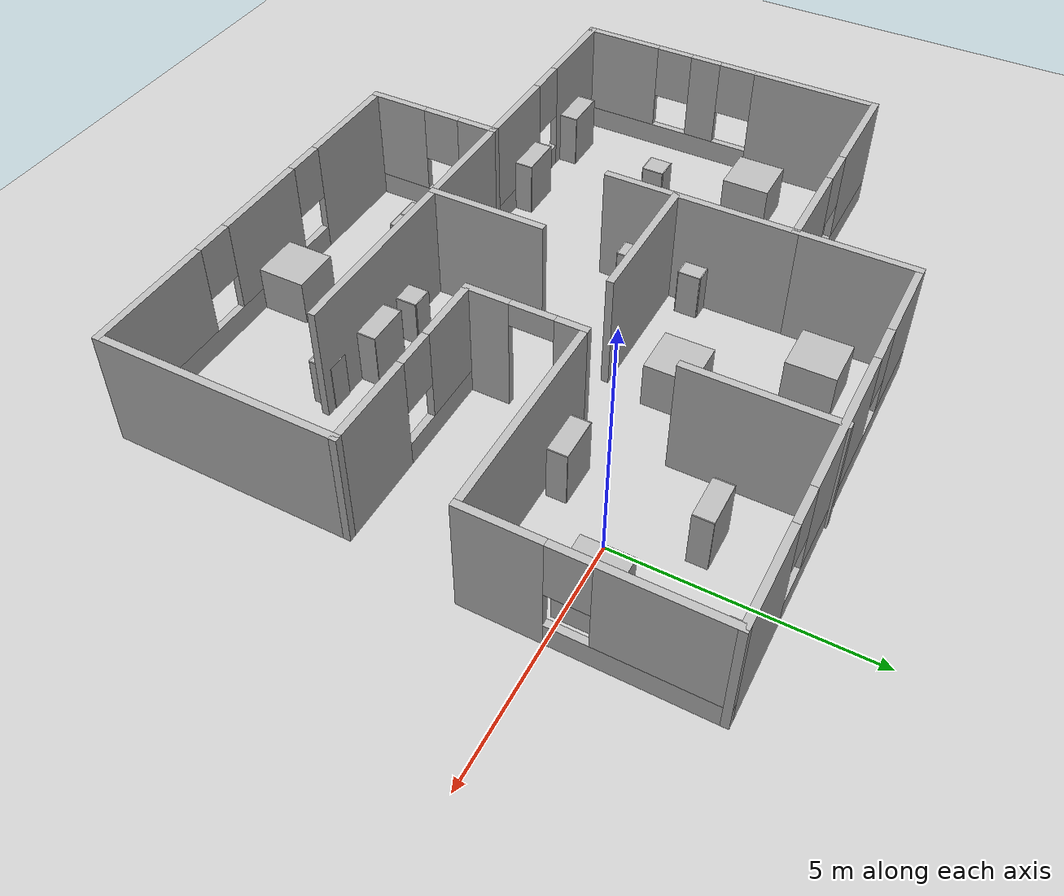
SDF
<sdf version="1.7">
 <world name="default">
  <light name="sun" type="directional">
   <pose>0 0 10 0 -0 0</pose>
   <diffuse>0.8 0.8 0.8 1</diffuse>
   <specular>0.2 0.2 0.2 1</specular>
   <attenuation>
    <range>1000</range>
    <constant>0.9</constant>
    <linear>0.01</linear>
    <quadratic>0.001</quadratic>
   </attenuation>
   <direction>-0.5 0.1 -0.9</direction>
   <spot><inner_angle>0</inner_angle><outer_angle>0</outer_angle><falloff>0</falloff></spot>
  </light>
  <model name="ground_plane">
   <static>1</static>
   <link name="link">
    <collision name="collision">
     <geometry><plane><normal>0 0 1</normal><size>100 100</size></plane></geometry>
     <surface><friction><ode><mu>100</mu><mu2>50</mu2></ode></friction></surface>
    </collision>
    <visual name="visual">
     <cast_shadows>0</cast_shadows>
     <geometry><plane><normal>0 0 1</normal><size>100 100</size></plane></geometry>
    </visual>
   </link>
  </model>
  <gravity>0 0 -9.8</gravity>
  <magnetic_field>6e-06 2.3e-05 -4.2e-05</magnetic_field>
  <atmosphere type="adiabatic"/>
  <physics type="ode">
   <max_step_size>0.001</max_step_size>
   <real_time_factor>1</real_time_factor>
   <real_time_update_rate>1000</real_time_update_rate>
  </physics>
  <scene><ambient>0.4 0.4 0.4 1</ambient><background>0.7 0.7 0.7 1</background><shadows>1</shadows></scene>
  <audio><device>default</device></audio>
  <spherical_coordinates>
   <surface_model>EARTH_WGS84</surface_model>
   <latitude_deg>0</latitude_deg>
   <longitude_deg>0</longitude_deg>
   <elevation>0</elevation>
   <heading_deg>0</heading_deg>
  </spherical_coordinates>
  <model name="room">
   <pose>-4.625 -2.82814 0 0 -0 0</pose>
   <link name="Wall_0">
    <collision name="Wall_0_Collision">
     <geometry><box><size>4.5 0.15 2.5</size></box></geometry>
     <pose>0 0 1.25 0 -0 0</pose>
    </collision>
    <visual name="Wall_0_Visual">
     <pose>0 0 1.25 0 -0 0</pose>
     <geometry><box><size>4.5 0.15 2.5</size></box></geometry>
     <ambient>1 1 1 1</ambient>
     <meta><layer>0</layer></meta>
    </visual>
    <pose>4.55 1.27814 0 0 -0 0</pose>
   </link>
   <link name="Wall_1">
    <pose>6.725 3.57814 0 0 -0 1.5708</pose>
    <visual name="Wall_1_Visual_0">
     <pose>-1.57759 0 1.25 0 -0 0</pose>
     <geometry><box><size>1.59481 0.15 2.5</size></box></geometry>
     <ambient>1 1 1 1</ambient>
     <meta><layer>0</layer></meta>
    </visual>
    <collision name="Wall_1_Collision_0">
     <geometry><box><size>1.59481 0.15 2.5</size></box></geometry>
     <pose>-1.57759 0 1.25 0 -0 0</pose>
    </collision>
    <visual name="Wall_1_Visual_1">
     <pose>0.797406 0 0.25 0 -0 0</pose>
     <geometry><box><size>3.15519 0.15 0.5</size></box></geometry>
     <ambient>1 1 1 1</ambient>
     <meta><layer>0</layer></meta>
    </visual>
    <collision name="Wall_1_Collision_1">
     <geometry><box><size>3.15519 0.15 0.5</size></box></geometry>
     <pose>0.797406 0 0.25 0 -0 0</pose>
    </collision>
    <visual name="Wall_1_Visual_2">
     <pose>1.19741 0 1.5 0 -0 0</pose>
     <geometry><box><size>2.35519 0.15 2</size></box></geometry>
     <ambient>1 1 1 1</ambient>
     <meta><layer>0</layer></meta>
    </visual>
    <collision name="Wall_1_Collision_2">
     <geometry><box><size>2.35519 0.15 2</size></box></geometry>
     <pose>1.19741 0 1.5 0 -0 0</pose>
    </collision>
    <visual name="Wall_1_Visual_3">
     <pose>-0.380187 0 1.9 0 -0 0</pose>
     <geometry><box><size>0.8 0.15 1.2</size></box></geometry>
     <ambient>1 1 1 1</ambient>
     <meta><layer>0</layer></meta>
    </visual>
    <collision name="Wall_1_Collision_3">
     <geometry><box><size>0.8 0.15 1.2</size></box></geometry>
     <pose>-0.380187 0 1.9 0 -0 0</pose>
    </collision>
   </link>
   <link name="Wall_10">
    <pose>4.425 -1.07186 0 0 -0 3.14159</pose>
    <visual name="Wall_10_Visual_0">
     <pose>-1.13522 0 1.25 0 -0 0</pose>
     <geometry><box><size>1.97956 0.15 2.5</size></box></geometry>
     <ambient>1 1 1 1</ambient>
     <meta><layer>0</layer></meta>
    </visual>
    <collision name="Wall_10_Collision_0">
     <geometry><box><size>1.97956 0.15 2.5</size></box></geometry>
     <pose>-1.13522 0 1.25 0 -0 0</pose>
    </collision>
    <visual name="Wall_10_Visual_1">
     <pose>0.989779 0 0.25 0 -0 0</pose>
     <geometry><box><size>2.27044 0.15 0.5</size></box></geometry>
     <ambient>1 1 1 1</ambient>
     <meta><layer>0</layer></meta>
    </visual>
    <collision name="Wall_10_Collision_1">
     <geometry><box><size>2.27044 0.15 0.5</size></box></geometry>
     <pose>0.989779 0 0.25 0 -0 0</pose>
    </collision>
    <visual name="Wall_10_Visual_2">
     <pose>1.38978 0 1.5 0 -0 0</pose>
     <geometry><box><size>1.47044 0.15 2</size></box></geometry>
     <ambient>1 1 1 1</ambient>
     <meta><layer>0</layer></meta>
    </visual>
    <collision name="Wall_10_Collision_2">
     <geometry><box><size>1.47044 0.15 2</size></box></geometry>
     <pose>1.38978 0 1.5 0 -0 0</pose>
    </collision>
    <visual name="Wall_10_Visual_3">
     <pose>0.254559 0 1.9 0 -0 0</pose>
     <geometry><box><size>0.8 0.15 1.2</size></box></geometry>
     <ambient>1 1 1 1</ambient>
     <meta><layer>0</layer></meta>
    </visual>
    <collision name="Wall_10_Collision_3">
     <geometry><box><size>0.8 0.15 1.2</size></box></geometry>
     <pose>0.254559 0 1.9 0 -0 0</pose>
    </collision>
   </link>
   <link name="Wall_12">
    <pose>2.375 0.103141 0 0 -0 1.5708</pose>
    <visual name="Wall_12_Visual_0">
     <pose>-0.77485 0 1.25 0 -0 0</pose>
     <geometry><box><size>0.950299 0.15 2.5</size></box></geometry>
     <ambient>1 1 1 1</ambient>
     <meta><layer>0</layer></meta>
    </visual>
    <collision name="Wall_12_Collision_0">
     <geometry><box><size>0.950299 0.15 2.5</size></box></geometry>
     <pose>-0.77485 0 1.25 0 -0 0</pose>
    </collision>
    <visual name="Wall_12_Visual_1">
     <pose>0.92515 0 1.25 0 -0 0</pose>
     <geometry><box><size>0.649701 0.15 2.5</size></box></geometry>
     <ambient>1 1 1 1</ambient>
     <meta><layer>0</layer></meta>
    </visual>
    <collision name="Wall_12_Collision_1">
     <geometry><box><size>0.649701 0.15 2.5</size></box></geometry>
     <pose>0.92515 0 1.25 0 -0 0</pose>
    </collision>
    <visual name="Wall_12_Visual_2">
     <pose>0.150299 0 2.25 0 -0 0</pose>
     <geometry><box><size>0.9 0.15 0.5</size></box></geometry>
     <ambient>1 1 1 1</ambient>
     <meta><layer>0</layer></meta>
    </visual>
    <collision name="Wall_12_Collision_2">
     <geometry><box><size>0.9 0.15 0.5</size></box></geometry>
     <pose>0.150299 0 2.25 0 -0 0</pose>
    </collision>
   </link>
   <link name="Wall_14">
    <collision name="Wall_14_Collision">
     <geometry><box><size>4 0.15 2.5</size></box></geometry>
     <pose>0 0 1.25 0 -0 0</pose>
    </collision>
    <visual name="Wall_14_Visual">
     <pose>0 0 1.25 0 -0 0</pose>
     <geometry><box><size>4 0.15 2.5</size></box></geometry>
     <ambient>1 1 1 1</ambient>
     <meta><layer>0</layer></meta>
    </visual>
    <pose>-1.875 1.60314 0 0 -0 -1.5708</pose>
   </link>
   <link name="Wall_16">
    <collision name="Wall_16_Collision">
     <geometry><box><size>3 0.15 2.5</size></box></geometry>
     <pose>0 0 1.25 0 -0 0</pose>
    </collision>
    <visual name="Wall_16_Visual">
     <pose>0 0 1.25 0 -0 0</pose>
     <geometry><box><size>3 0.15 2.5</size></box></geometry>
     <ambient>1 1 1 1</ambient>
     <meta><layer>0</layer></meta>
    </visual>
    <pose>2.38903 4.49686 0 0 -0 -1.5708</pose>
   </link>
   <link name="Wall_18">
    <collision name="Wall_18_Collision">
     <geometry><box><size>6.5 0.15 2.5</size></box></geometry>
     <pose>0 0 1.25 0 -0 0</pose>
    </collision>
    <visual name="Wall_18_Visual">
     <pose>0 0 1.25 0 -0 0</pose>
     <geometry><box><size>6.5 0.15 2.5</size></box></geometry>
     <ambient>1 1 1 1</ambient>
     <meta><layer>0</layer></meta>
    </visual>
    <pose>1.05 -3.07186 0 0 -0 0</pose>
   </link>
   <link name="Wall_2">
    <pose>2.425 5.87814 0 0 -0 3.14159</pose>
    <visual name="Wall_2_Visual_0">
     <pose>-3.30712 0 1.25 0 -0 0</pose>
     <geometry><box><size>2.13576 0.15 2.5</size></box></geometry>
     <ambient>1 1 1 1</ambient>
     <meta><layer>0</layer></meta>
    </visual>
    <collision name="Wall_2_Collision_0">
     <geometry><box><size>2.13576 0.15 2.5</size></box></geometry>
     <pose>-3.30712 0 1.25 0 -0 0</pose>
    </collision>
    <visual name="Wall_2_Visual_1">
     <pose>1.06788 0 0.25 0 -0 0</pose>
     <geometry><box><size>6.61424 0.15 0.5</size></box></geometry>
     <ambient>1 1 1 1</ambient>
     <meta><layer>0</layer></meta>
    </visual>
    <collision name="Wall_2_Collision_1">
     <geometry><box><size>6.61424 0.15 0.5</size></box></geometry>
     <pose>1.06788 0 0.25 0 -0 0</pose>
    </collision>
    <visual name="Wall_2_Visual_2">
     <pose>0.145143 0 1.5 0 -0 0</pose>
     <geometry><box><size>3.16877 0.15 2</size></box></geometry>
     <ambient>1 1 1 1</ambient>
     <meta><layer>0</layer></meta>
    </visual>
    <collision name="Wall_2_Collision_2">
     <geometry><box><size>3.16877 0.15 2</size></box></geometry>
     <pose>0.145143 0 1.5 0 -0 0</pose>
    </collision>
    <visual name="Wall_2_Visual_3">
     <pose>3.45226 0 1.5 0 -0 0</pose>
     <geometry><box><size>1.84547 0.15 2</size></box></geometry>
     <ambient>1 1 1 1</ambient>
     <meta><layer>0</layer></meta>
    </visual>
    <collision name="Wall_2_Collision_3">
     <geometry><box><size>1.84547 0.15 2</size></box></geometry>
     <pose>3.45226 0 1.5 0 -0 0</pose>
    </collision>
    <visual name="Wall_2_Visual_4">
     <pose>-1.83924 0 1.9 0 -0 0</pose>
     <geometry><box><size>0.8 0.15 1.2</size></box></geometry>
     <ambient>1 1 1 1</ambient>
     <meta><layer>0</layer></meta>
    </visual>
    <collision name="Wall_2_Collision_4">
     <geometry><box><size>0.8 0.15 1.2</size></box></geometry>
     <pose>-1.83924 0 1.9 0 -0 0</pose>
    </collision>
    <visual name="Wall_2_Visual_5">
     <pose>2.12953 0 1.9 0 -0 0</pose>
     <geometry><box><size>0.8 0.15 1.2</size></box></geometry>
     <ambient>1 1 1 1</ambient>
     <meta><layer>0</layer></meta>
    </visual>
    <collision name="Wall_2_Collision_5">
     <geometry><box><size>0.8 0.15 1.2</size></box></geometry>
     <pose>2.12953 0 1.9 0 -0 0</pose>
    </collision>
   </link>
   <link name="Wall_20">
    <collision name="Wall_20_Collision">
     <geometry><box><size>3 0.15 2.5</size></box></geometry>
     <pose>0 0 1.25 0 -0 0</pose>
    </collision>
    <visual name="Wall_20_Visual">
     <pose>0 0 1.25 0 -0 0</pose>
     <geometry><box><size>3 0.15 2.5</size></box></geometry>
     <ambient>1 1 1 1</ambient>
     <meta><layer>0</layer></meta>
    </visual>
    <pose>-0.433206 1.10833 0 0 -0 0</pose>
   </link>
   <link name="Wall_22">
    <collision name="Wall_22_Collision">
     <geometry><box><size>2.5 0.15 2.5</size></box></geometry>
     <pose>0 0 1.25 0 -0 0</pose>
    </collision>
    <visual name="Wall_22_Visual">
     <pose>0 0 1.25 0 -0 0</pose>
     <geometry><box><size>2.5 0.15 2.5</size></box></geometry>
     <ambient>1 1 1 1</ambient>
     <meta><layer>0</layer></meta>
    </visual>
    <pose>0.230018 -1.89312 0 0 -0 1.5708</pose>
   </link>
   <link name="Wall_3">
    <collision name="Wall_3_Collision">
     <geometry><box><size>2.5 0.15 2.5</size></box></geometry>
     <pose>0 0 1.25 0 -0 0</pose>
    </collision>
    <visual name="Wall_3_Visual">
     <pose>0 0 1.25 0 -0 0</pose>
     <geometry><box><size>2.5 0.15 2.5</size></box></geometry>
     <ambient>1 1 1 1</ambient>
     <meta><layer>0</layer></meta>
    </visual>
    <pose>-1.875 4.70314 0 0 -0 -1.5708</pose>
   </link>
   <link name="Wall_4">
    <pose>-4.3 3.52814 0 0 -0 3.14159</pose>
    <visual name="Wall_4_Visual_0">
     <pose>-1.50396 0 1.25 0 -0 0</pose>
     <geometry><box><size>1.99209 0.15 2.5</size></box></geometry>
     <ambient>1 1 1 1</ambient>
     <meta><layer>0</layer></meta>
    </visual>
    <collision name="Wall_4_Collision_0">
     <geometry><box><size>1.99209 0.15 2.5</size></box></geometry>
     <pose>-1.50396 0 1.25 0 -0 0</pose>
    </collision>
    <visual name="Wall_4_Visual_1">
     <pose>0.996043 0 0.25 0 -0 0</pose>
     <geometry><box><size>3.00791 0.15 0.5</size></box></geometry>
     <ambient>1 1 1 1</ambient>
     <meta><layer>0</layer></meta>
    </visual>
    <collision name="Wall_4_Collision_1">
     <geometry><box><size>3.00791 0.15 0.5</size></box></geometry>
     <pose>0.996043 0 0.25 0 -0 0</pose>
    </collision>
    <visual name="Wall_4_Visual_2">
     <pose>1.39604 0 1.5 0 -0 0</pose>
     <geometry><box><size>2.20791 0.15 2</size></box></geometry>
     <ambient>1 1 1 1</ambient>
     <meta><layer>0</layer></meta>
    </visual>
    <collision name="Wall_4_Collision_2">
     <geometry><box><size>2.20791 0.15 2</size></box></geometry>
     <pose>1.39604 0 1.5 0 -0 0</pose>
    </collision>
    <visual name="Wall_4_Visual_3">
     <pose>-0.107913 0 1.9 0 -0 0</pose>
     <geometry><box><size>0.8 0.15 1.2</size></box></geometry>
     <ambient>1 1 1 1</ambient>
     <meta><layer>0</layer></meta>
    </visual>
    <collision name="Wall_4_Collision_3">
     <geometry><box><size>0.8 0.15 1.2</size></box></geometry>
     <pose>-0.107913 0 1.9 0 -0 0</pose>
    </collision>
   </link>
   <link name="Wall_5">
    <pose>-6.725 0.228141 0 0 -0 -1.5708</pose>
    <visual name="Wall_5_Visual_0">
     <pose>-2.01057 0 1.25 0 -0 0</pose>
     <geometry><box><size>2.72885 0.15 2.5</size></box></geometry>
     <ambient>1 1 1 1</ambient>
     <meta><layer>0</layer></meta>
    </visual>
    <collision name="Wall_5_Collision_0">
     <geometry><box><size>2.72885 0.15 2.5</size></box></geometry>
     <pose>-2.01057 0 1.25 0 -0 0</pose>
    </collision>
    <visual name="Wall_5_Visual_1">
     <pose>1.36443 0 0.25 0 -0 0</pose>
     <geometry><box><size>4.02115 0.15 0.5</size></box></geometry>
     <ambient>1 1 1 1</ambient>
     <meta><layer>0</layer></meta>
    </visual>
    <collision name="Wall_5_Collision_1">
     <geometry><box><size>4.02115 0.15 0.5</size></box></geometry>
     <pose>1.36443 0 0.25 0 -0 0</pose>
    </collision>
    <visual name="Wall_5_Visual_2">
     <pose>0.493131 0 1.5 0 -0 0</pose>
     <geometry><box><size>0.67856 0.15 2</size></box></geometry>
     <ambient>1 1 1 1</ambient>
     <meta><layer>0</layer></meta>
    </visual>
    <collision name="Wall_5_Collision_2">
     <geometry><box><size>0.67856 0.15 2</size></box></geometry>
     <pose>0.493131 0 1.5 0 -0 0</pose>
    </collision>
    <visual name="Wall_5_Visual_3">
     <pose>2.50371 0 1.5 0 -0 0</pose>
     <geometry><box><size>1.74259 0.15 2</size></box></geometry>
     <ambient>1 1 1 1</ambient>
     <meta><layer>0</layer></meta>
    </visual>
    <collision name="Wall_5_Collision_3">
     <geometry><box><size>1.74259 0.15 2</size></box></geometry>
     <pose>2.50371 0 1.5 0 -0 0</pose>
    </collision>
    <visual name="Wall_5_Visual_4">
     <pose>-0.246149 0 1.9 0 -0 0</pose>
     <geometry><box><size>0.8 0.15 1.2</size></box></geometry>
     <ambient>1 1 1 1</ambient>
     <meta><layer>0</layer></meta>
    </visual>
    <collision name="Wall_5_Collision_4">
     <geometry><box><size>0.8 0.15 1.2</size></box></geometry>
     <pose>-0.246149 0 1.9 0 -0 0</pose>
    </collision>
    <visual name="Wall_5_Visual_5">
     <pose>1.23241 0 1.9 0 -0 0</pose>
     <geometry><box><size>0.8 0.15 1.2</size></box></geometry>
     <ambient>1 1 1 1</ambient>
     <meta><layer>0</layer></meta>
    </visual>
    <collision name="Wall_5_Collision_5">
     <geometry><box><size>0.8 0.15 1.2</size></box></geometry>
     <pose>1.23241 0 1.9 0 -0 0</pose>
    </collision>
   </link>
   <link name="Wall_6">
    <pose>-4.425 -3.07186 0 0 -0 0</pose>
    <visual name="Wall_6_Visual_0">
     <pose>-1.38777 0 1.25 0 -0 0</pose>
     <geometry><box><size>1.97446 0.15 2.5</size></box></geometry>
     <ambient>1 1 1 1</ambient>
     <meta><layer>0</layer></meta>
    </visual>
    <collision name="Wall_6_Collision_0">
     <geometry><box><size>1.97446 0.15 2.5</size></box></geometry>
     <pose>-1.38777 0 1.25 0 -0 0</pose>
    </collision>
    <visual name="Wall_6_Visual_1">
     <pose>0.987228 0 0.25 0 -0 0</pose>
     <geometry><box><size>2.77554 0.15 0.5</size></box></geometry>
     <ambient>1 1 1 1</ambient>
     <meta><layer>0</layer></meta>
    </visual>
    <collision name="Wall_6_Collision_1">
     <geometry><box><size>2.77554 0.15 0.5</size></box></geometry>
     <pose>0.987228 0 0.25 0 -0 0</pose>
    </collision>
    <visual name="Wall_6_Visual_2">
     <pose>1.38723 0 1.5 0 -0 0</pose>
     <geometry><box><size>1.97554 0.15 2</size></box></geometry>
     <ambient>1 1 1 1</ambient>
     <meta><layer>0</layer></meta>
    </visual>
    <collision name="Wall_6_Collision_2">
     <geometry><box><size>1.97554 0.15 2</size></box></geometry>
     <pose>1.38723 0 1.5 0 -0 0</pose>
    </collision>
    <visual name="Wall_6_Visual_3">
     <pose>-0.000544 0 1.9 0 -0 0</pose>
     <geometry><box><size>0.8 0.15 1.2</size></box></geometry>
     <ambient>1 1 1 1</ambient>
     <meta><layer>0</layer></meta>
    </visual>
    <collision name="Wall_6_Collision_3">
     <geometry><box><size>0.8 0.15 1.2</size></box></geometry>
     <pose>-0.000544 0 1.9 0 -0 0</pose>
    </collision>
   </link>
   <link name="Wall_7">
    <pose>-2.125 -4.49686 0 0 -0 -1.5708</pose>
    <visual name="Wall_7_Visual_0">
     <pose>-1.05214 0 1.25 0 -0 0</pose>
     <geometry><box><size>0.895729 0.15 2.5</size></box></geometry>
     <ambient>1 1 1 1</ambient>
     <meta><layer>0</layer></meta>
    </visual>
    <collision name="Wall_7_Collision_0">
     <geometry><box><size>0.895729 0.15 2.5</size></box></geometry>
     <pose>-1.05214 0 1.25 0 -0 0</pose>
    </collision>
    <visual name="Wall_7_Visual_1">
     <pose>0.447864 0 0.25 0 -0 0</pose>
     <geometry><box><size>2.10427 0.15 0.5</size></box></geometry>
     <ambient>1 1 1 1</ambient>
     <meta><layer>0</layer></meta>
    </visual>
    <collision name="Wall_7_Collision_1">
     <geometry><box><size>2.10427 0.15 0.5</size></box></geometry>
     <pose>0.447864 0 0.25 0 -0 0</pose>
    </collision>
    <visual name="Wall_7_Visual_2">
     <pose>0.847864 0 1.5 0 -0 0</pose>
     <geometry><box><size>1.30427 0.15 2</size></box></geometry>
     <ambient>1 1 1 1</ambient>
     <meta><layer>0</layer></meta>
    </visual>
    <collision name="Wall_7_Collision_2">
     <geometry><box><size>1.30427 0.15 2</size></box></geometry>
     <pose>0.847864 0 1.5 0 -0 0</pose>
    </collision>
    <visual name="Wall_7_Visual_3">
     <pose>-0.204271 0 1.9 0 -0 0</pose>
     <geometry><box><size>0.8 0.15 1.2</size></box></geometry>
     <ambient>1 1 1 1</ambient>
     <meta><layer>0</layer></meta>
    </visual>
    <collision name="Wall_7_Collision_3">
     <geometry><box><size>0.8 0.15 1.2</size></box></geometry>
     <pose>-0.204271 0 1.9 0 -0 0</pose>
    </collision>
   </link>
   <link name="Wall_8">
    <pose>2.175 -5.92186 0 0 -0 0</pose>
    <visual name="Wall_8_Visual_0">
     <pose>-3.2051 0 1.25 0 -0 0</pose>
     <geometry><box><size>2.33979 0.15 2.5</size></box></geometry>
     <ambient>1 1 1 1</ambient>
     <meta><layer>0</layer></meta>
    </visual>
    <collision name="Wall_8_Collision_0">
     <geometry><box><size>2.33979 0.15 2.5</size></box></geometry>
     <pose>-3.2051 0 1.25 0 -0 0</pose>
    </collision>
    <visual name="Wall_8_Visual_1">
     <pose>1.1699 0 0.25 0 -0 0</pose>
     <geometry><box><size>6.41021 0.15 0.5</size></box></geometry>
     <ambient>1 1 1 1</ambient>
     <meta><layer>0</layer></meta>
    </visual>
    <collision name="Wall_8_Collision_1">
     <geometry><box><size>6.41021 0.15 0.5</size></box></geometry>
     <pose>1.1699 0 0.25 0 -0 0</pose>
    </collision>
    <visual name="Wall_8_Visual_2">
     <pose>-0.193626 0 1.5 0 -0 0</pose>
     <geometry><box><size>2.08316 0.15 2</size></box></geometry>
     <ambient>1 1 1 1</ambient>
     <meta><layer>0</layer></meta>
    </visual>
    <collision name="Wall_8_Collision_2">
     <geometry><box><size>2.08316 0.15 2</size></box></geometry>
     <pose>-0.193626 0 1.5 0 -0 0</pose>
    </collision>
    <visual name="Wall_8_Visual_3">
     <pose>3.01148 0 1.5 0 -0 0</pose>
     <geometry><box><size>2.72704 0.15 2</size></box></geometry>
     <ambient>1 1 1 1</ambient>
     <meta><layer>0</layer></meta>
    </visual>
    <collision name="Wall_8_Collision_3">
     <geometry><box><size>2.72704 0.15 2</size></box></geometry>
     <pose>3.01148 0 1.5 0 -0 0</pose>
    </collision>
    <visual name="Wall_8_Visual_4">
     <pose>-1.63521 0 1.9 0 -0 0</pose>
     <geometry><box><size>0.8 0.15 1.2</size></box></geometry>
     <ambient>1 1 1 1</ambient>
     <meta><layer>0</layer></meta>
    </visual>
    <collision name="Wall_8_Collision_4">
     <geometry><box><size>0.8 0.15 1.2</size></box></geometry>
     <pose>-1.63521 0 1.9 0 -0 0</pose>
    </collision>
    <visual name="Wall_8_Visual_5">
     <pose>1.24795 0 1.9 0 -0 0</pose>
     <geometry><box><size>0.8 0.15 1.2</size></box></geometry>
     <ambient>1 1 1 1</ambient>
     <meta><layer>0</layer></meta>
    </visual>
    <collision name="Wall_8_Collision_5">
     <geometry><box><size>0.8 0.15 1.2</size></box></geometry>
     <pose>1.24795 0 1.9 0 -0 0</pose>
    </collision>
   </link>
   <link name="Wall_9">
    <collision name="Wall_9_Collision">
     <geometry><box><size>5 0.15 2.5</size></box></geometry>
     <pose>0 0 1.25 0 -0 0</pose>
    </collision>
    <visual name="Wall_9_Visual">
     <pose>0 0 1.25 0 -0 0</pose>
     <geometry><box><size>5 0.15 2.5</size></box></geometry>
     <ambient>1 1 1 1</ambient>
     <meta><layer>0</layer></meta>
    </visual>
    <pose>6.475 -3.49686 0 0 -0 1.5708</pose>
   </link>
   <static>1</static>
  </model>
  <model name="bookshelf">
   <static>1</static>
   <link name="link">
    <inertial><mass>1</mass></inertial>
    <collision name="back">
     <pose>0 0.005 0.6 0 -0 0</pose>
     <geometry><box><size>0.9 0.01 1.2</size></box></geometry>
    </collision>
    <visual name="visual1">
     <pose>0 0.005 0.6 0 -0 0</pose>
     <geometry><box><size>0.9 0.01 1.2</size></box></geometry>
    </visual>
    <collision name="left_side">
     <pose>0.45 -0.195 0.6 0 -0 0</pose>
     <geometry><box><size>0.02 0.4 1.2</size></box></geometry>
    </collision>
    <visual name="visual2">
     <pose>0.45 -0.195 0.6 0 -0 0</pose>
     <geometry><box><size>0.02 0.4 1.2</size></box></geometry>
    </visual>
    <collision name="right_side">
     <pose>-0.45 -0.195 0.6 0 -0 0</pose>
     <geometry><box><size>0.02 0.4 1.2</size></box></geometry>
    </collision>
    <visual name="visual3">
     <pose>-0.45 -0.195 0.6 0 -0 0</pose>
     <geometry><box><size>0.02 0.4 1.2</size></box></geometry>
    </visual>
    <collision name="bottom">
     <pose>0 -0.195 0.03 0 -0 0</pose>
     <geometry><box><size>0.88 0.4 0.06</size></box></geometry>
    </collision>
    <visual name="visual4">
     <pose>0 -0.195 0.03 0 -0 0</pose>
     <geometry><box><size>0.88 0.4 0.06</size></box></geometry>
    </visual>
    <collision name="top">
     <pose>0 -0.195 1.19 0 -0 0</pose>
     <geometry><box><size>0.88 0.4 0.02</size></box></geometry>
    </collision>
    <visual name="visual5">
     <pose>0 -0.195 1.19 0 -0 0</pose>
     <geometry><box><size>0.88 0.4 0.02</size></box></geometry>
    </visual>
    <collision name="low_shelf">
     <pose>0 -0.195 0.43 0 -0 0</pose>
     <geometry><box><size>0.88 0.4 0.02</size></box></geometry>
    </collision>
    <visual name="visual6">
     <pose>0 -0.195 0.43 0 -0 0</pose>
     <geometry><box><size>0.88 0.4 0.02</size></box></geometry>
    </visual>
    <collision name="high_shelf">
     <pose>0 -0.195 0.8 0 -0 0</pose>
     <geometry><box><size>0.88 0.4 0.02</size></box></geometry>
    </collision>
    <visual name="visual7">
     <pose>0 -0.195 0.8 0 -0 0</pose>
     <geometry><box><size>0.88 0.4 0.02</size></box></geometry>
    </visual>
   </link>
   <pose>-10.1033 -5.42318 0 0 -0 0</pose>
  </model>
  <model name="bookshelf_0">
   <static>1</static>
   <link name="link">
    <inertial><mass>1</mass></inertial>
    <collision name="back">
     <pose>0 0.005 0.6 0 -0 0</pose>
     <geometry><box><size>0.9 0.01 1.2</size></box></geometry>
    </collision>
    <visual name="visual1">
     <pose>0 0.005 0.6 0 -0 0</pose>
     <geometry><box><size>0.9 0.01 1.2</size></box></geometry>
    </visual>
    <collision name="left_side">
     <pose>0.45 -0.195 0.6 0 -0 0</pose>
     <geometry><box><size>0.02 0.4 1.2</size></box></geometry>
    </collision>
    <visual name="visual2">
     <pose>0.45 -0.195 0.6 0 -0 0</pose>
     <geometry><box><size>0.02 0.4 1.2</size></box></geometry>
    </visual>
    <collision name="right_side">
     <pose>-0.45 -0.195 0.6 0 -0 0</pose>
     <geometry><box><size>0.02 0.4 1.2</size></box></geometry>
    </collision>
    <visual name="visual3">
     <pose>-0.45 -0.195 0.6 0 -0 0</pose>
     <geometry><box><size>0.02 0.4 1.2</size></box></geometry>
    </visual>
    <collision name="bottom">
     <pose>0 -0.195 0.03 0 -0 0</pose>
     <geometry><box><size>0.88 0.4 0.06</size></box></geometry>
    </collision>
    <visual name="visual4">
     <pose>0 -0.195 0.03 0 -0 0</pose>
     <geometry><box><size>0.88 0.4 0.06</size></box></geometry>
    </visual>
    <collision name="top">
     <pose>0 -0.195 1.19 0 -0 0</pose>
     <geometry><box><size>0.88 0.4 0.02</size></box></geometry>
    </collision>
    <visual name="visual5">
     <pose>0 -0.195 1.19 0 -0 0</pose>
     <geometry><box><size>0.88 0.4 0.02</size></box></geometry>
    </visual>
    <collision name="low_shelf">
     <pose>0 -0.195 0.43 0 -0 0</pose>
     <geometry><box><size>0.88 0.4 0.02</size></box></geometry>
    </collision>
    <visual name="visual6">
     <pose>0 -0.195 0.43 0 -0 0</pose>
     <geometry><box><size>0.88 0.4 0.02</size></box></geometry>
    </visual>
    <collision name="high_shelf">
     <pose>0 -0.195 0.8 0 -0 0</pose>
     <geometry><box><size>0.88 0.4 0.02</size></box></geometry>
    </collision>
    <visual name="visual7">
     <pose>0 -0.195 0.8 0 -0 0</pose>
     <geometry><box><size>0.88 0.4 0.02</size></box></geometry>
    </visual>
   </link>
   <pose>-8.00371 -5.4438 0 0 -0 0</pose>
  </model>
  <model name="cabinet">
   <static>1</static>
   <link name="cabinet_bottom_plate">
    <inertial>
     <pose>0 0 -1 0 -0 0</pose>
     <inertia><ixx>2.05</ixx><ixy>0</ixy><ixz>0</ixz><iyy>2.05</iyy><iyz>0</iyz><izz>2.05</izz></inertia>
     <mass>25</mass>
    </inertial>
    <collision name="cabinet_bottom_plate_geom">
     <pose>0 0 0.01 0 -0 0</pose>
     <geometry><box><size>0.45 0.45 0.02</size></box></geometry>
    </collision>
    <visual name="cabinet_bottom_plate_geom_visual">
     <pose>0 0 0.01 0 -0 0</pose>
     <geometry><box><size>0.45 0.45 0.02</size></box></geometry>
    </visual>
    <collision name="cabinet_bottom_plate_geom_cabinet_back_plate">
     <pose>0.235 0 0.51 0 -0 0</pose>
     <geometry><box><size>0.02 0.45 1.02</size></box></geometry>
    </collision>
    <visual name="cabinet_bottom_plate_geom_cabinet_back_plate_visual">
     <pose>0.235 0 0.51 0 -0 0</pose>
     <geometry><box><size>0.02 0.45 1.02</size></box></geometry>
    </visual>
    <collision name="cabinet_bottom_plate_geom_cabinet_left_plate">
     <pose>0 0.235 0.51 0 -0 0</pose>
     <geometry><box><size>0.45 0.02 1.02</size></box></geometry>
    </collision>
    <visual name="cabinet_bottom_plate_geom_cabinet_left_plate_visual">
     <pose>0 0.235 0.51 0 -0 0</pose>
     <geometry><box><size>0.45 0.02 1.02</size></box></geometry>
    </visual>
    <collision name="cabinet_bottom_plate_geom_cabinet_middle_plate">
     <pose>0 0 0.51 0 -0 0</pose>
     <geometry><box><size>0.45 0.45 0.02</size></box></geometry>
    </collision>
    <visual name="cabinet_bottom_plate_geom_cabinet_middle_plate_visual">
     <pose>0 0 0.51 0 -0 0</pose>
     <geometry><box><size>0.45 0.45 0.02</size></box></geometry>
    </visual>
    <collision name="cabinet_bottom_plate_geom_cabinet_right_plate">
     <pose>0 -0.235 0.51 0 -0 0</pose>
     <geometry><box><size>0.45 0.02 1.02</size></box></geometry>
    </collision>
    <visual name="cabinet_bottom_plate_geom_cabinet_right_plate_visual">
     <pose>0 -0.235 0.51 0 -0 0</pose>
     <geometry><box><size>0.45 0.02 1.02</size></box></geometry>
    </visual>
    <collision name="cabinet_bottom_plate_geom_cabinet_top_plate">
     <pose>0 0 1.01 0 -0 0</pose>
     <geometry><box><size>0.45 0.45 0.02</size></box></geometry>
    </collision>
    <visual name="cabinet_bottom_plate_geom_cabinet_top_plate_visual">
     <pose>0 0 1.01 0 -0 0</pose>
     <geometry><box><size>0.45 0.45 0.02</size></box></geometry>
    </visual>
   </link>
   <pose>-9.13971 -3.19511 0 0 -0 0</pose>
  </model>
  <model name="bookshelf_1">
   <static>1</static>
   <link name="link">
    <inertial><mass>1</mass></inertial>
    <collision name="back">
     <pose>0 0.005 0.6 0 -0 0</pose>
     <geometry><box><size>0.9 0.01 1.2</size></box></geometry>
    </collision>
    <visual name="visual1">
     <pose>0 0.005 0.6 0 -0 0</pose>
     <geometry><box><size>0.9 0.01 1.2</size></box></geometry>
    </visual>
    <collision name="left_side">
     <pose>0.45 -0.195 0.6 0 -0 0</pose>
     <geometry><box><size>0.02 0.4 1.2</size></box></geometry>
    </collision>
    <visual name="visual2">
     <pose>0.45 -0.195 0.6 0 -0 0</pose>
     <geometry><box><size>0.02 0.4 1.2</size></box></geometry>
    </visual>
    <collision name="right_side">
     <pose>-0.45 -0.195 0.6 0 -0 0</pose>
     <geometry><box><size>0.02 0.4 1.2</size></box></geometry>
    </collision>
    <visual name="visual3">
     <pose>-0.45 -0.195 0.6 0 -0 0</pose>
     <geometry><box><size>0.02 0.4 1.2</size></box></geometry>
    </visual>
    <collision name="bottom">
     <pose>0 -0.195 0.03 0 -0 0</pose>
     <geometry><box><size>0.88 0.4 0.06</size></box></geometry>
    </collision>
    <visual name="visual4">
     <pose>0 -0.195 0.03 0 -0 0</pose>
     <geometry><box><size>0.88 0.4 0.06</size></box></geometry>
    </visual>
    <collision name="top">
     <pose>0 -0.195 1.19 0 -0 0</pose>
     <geometry><box><size>0.88 0.4 0.02</size></box></geometry>
    </collision>
    <visual name="visual5">
     <pose>0 -0.195 1.19 0 -0 0</pose>
     <geometry><box><size>0.88 0.4 0.02</size></box></geometry>
    </visual>
    <collision name="low_shelf">
     <pose>0 -0.195 0.43 0 -0 0</pose>
     <geometry><box><size>0.88 0.4 0.02</size></box></geometry>
    </collision>
    <visual name="visual6">
     <pose>0 -0.195 0.43 0 -0 0</pose>
     <geometry><box><size>0.88 0.4 0.02</size></box></geometry>
    </visual>
    <collision name="high_shelf">
     <pose>0 -0.195 0.8 0 -0 0</pose>
     <geometry><box><size>0.88 0.4 0.02</size></box></geometry>
    </collision>
    <visual name="visual7">
     <pose>0 -0.195 0.8 0 -0 0</pose>
     <geometry><box><size>0.88 0.4 0.02</size></box></geometry>
    </visual>
   </link>
   <pose>-9.85971 0.62305 0 0 -0 0</pose>
  </model>
  <model name="bookshelf_2">
   <static>1</static>
   <link name="link">
    <inertial><mass>1</mass></inertial>
    <collision name="back">
     <pose>0 0.005 0.6 0 -0 0</pose>
     <geometry><box><size>0.9 0.01 1.2</size></box></geometry>
    </collision>
    <visual name="visual1">
     <pose>0 0.005 0.6 0 -0 0</pose>
     <geometry><box><size>0.9 0.01 1.2</size></box></geometry>
    </visual>
    <collision name="left_side">
     <pose>0.45 -0.195 0.6 0 -0 0</pose>
     <geometry><box><size>0.02 0.4 1.2</size></box></geometry>
    </collision>
    <visual name="visual2">
     <pose>0.45 -0.195 0.6 0 -0 0</pose>
     <geometry><box><size>0.02 0.4 1.2</size></box></geometry>
    </visual>
    <collision name="right_side">
     <pose>-0.45 -0.195 0.6 0 -0 0</pose>
     <geometry><box><size>0.02 0.4 1.2</size></box></geometry>
    </collision>
    <visual name="visual3">
     <pose>-0.45 -0.195 0.6 0 -0 0</pose>
     <geometry><box><size>0.02 0.4 1.2</size></box></geometry>
    </visual>
    <collision name="bottom">
     <pose>0 -0.195 0.03 0 -0 0</pose>
     <geometry><box><size>0.88 0.4 0.06</size></box></geometry>
    </collision>
    <visual name="visual4">
     <pose>0 -0.195 0.03 0 -0 0</pose>
     <geometry><box><size>0.88 0.4 0.06</size></box></geometry>
    </visual>
    <collision name="top">
     <pose>0 -0.195 1.19 0 -0 0</pose>
     <geometry><box><size>0.88 0.4 0.02</size></box></geometry>
    </collision>
    <visual name="visual5">
     <pose>0 -0.195 1.19 0 -0 0</pose>
     <geometry><box><size>0.88 0.4 0.02</size></box></geometry>
    </visual>
    <collision name="low_shelf">
     <pose>0 -0.195 0.43 0 -0 0</pose>
     <geometry><box><size>0.88 0.4 0.02</size></box></geometry>
    </collision>
    <visual name="visual6">
     <pose>0 -0.195 0.43 0 -0 0</pose>
     <geometry><box><size>0.88 0.4 0.02</size></box></geometry>
    </visual>
    <collision name="high_shelf">
     <pose>0 -0.195 0.8 0 -0 0</pose>
     <geometry><box><size>0.88 0.4 0.02</size></box></geometry>
    </collision>
    <visual name="visual7">
     <pose>0 -0.195 0.8 0 -0 0</pose>
     <geometry><box><size>0.88 0.4 0.02</size></box></geometry>
    </visual>
   </link>
   <pose>-7.01224 -1.28845 0 0 -0 0</pose>
  </model>
  <model name="unit_box">
   <pose>-9.84962 -1.23182 0.5 0 -0 0</pose>
   <link name="link">
    <inertial>
     <mass>1</mass>
     <inertia>
      <ixx>0.166667</ixx>
      <ixy>0</ixy>
      <ixz>0</ixz>
      <iyy>0.166667</iyy>
      <iyz>0</iyz>
      <izz>0.166667</izz>
     </inertia>
    </inertial>
    <collision name="collision"><geometry><box><size>1 1 1</size></box></geometry></collision>
    <visual name="visual"><geometry><box><size>1 1 1</size></box></geometry></visual>
   </link>
  </model>
  <model name="unit_cylinder">
   <pose>-4.97663 -5.32499 0.499992 -3e-06 4e-06 0</pose>
   <link name="link">
    <inertial>
     <mass>1</mass>
     <inertia><ixx>0.145833</ixx><ixy>0</ixy><ixz>0</ixz><iyy>0.145833</iyy><iyz>0</iyz><izz>0.125</izz></inertia>
    </inertial>
    <collision name="collision">
     <geometry><cylinder><radius>0.5</radius><length>1</length></cylinder></geometry>
    </collision>
    <visual name="visual">
     <geometry><cylinder><radius>0.5</radius><length>1</length></cylinder></geometry>
    </visual>
   </link>
  </model>
  <model name="unit_box_0">
   <pose>-5.15311 1.86707 0.5 0 -0 0</pose>
   <link name="link">
    <inertial>
     <mass>1</mass>
     <inertia>
      <ixx>0.166667</ixx>
      <ixy>0</ixy>
      <ixz>0</ixz>
      <iyy>0.166667</iyy>
      <iyz>0</iyz>
      <izz>0.166667</izz>
     </inertia>
    </inertial>
    <collision name="collision"><geometry><box><size>1 1 1</size></box></geometry></collision>
    <visual name="visual"><geometry><box><size>1 1 1</size></box></geometry></visual>
   </link>
  </model>
  <model name="unit_box_1">
   <pose>1.15759 0.350175 0.5 0 -0 0</pose>
   <link name="link">
    <inertial>
     <mass>1</mass>
     <inertia>
      <ixx>0.166667</ixx>
      <ixy>0</ixy>
      <ixz>0</ixz>
      <iyy>0.166667</iyy>
      <iyz>0</iyz>
      <izz>0.166667</izz>
     </inertia>
    </inertial>
    <collision name="collision"><geometry><box><size>1 1 1</size></box></geometry></collision>
    <visual name="visual"><geometry><box><size>1 1 1</size></box></geometry></visual>
   </link>
  </model>
  <model name="bookshelf_3">
   <static>1</static>
   <link name="link">
    <inertial><mass>1</mass></inertial>
    <collision name="back">
     <pose>0 0.005 0.6 0 -0 0</pose>
     <geometry><box><size>0.9 0.01 1.2</size></box></geometry>
    </collision>
    <visual name="visual1">
     <pose>0 0.005 0.6 0 -0 0</pose>
     <geometry><box><size>0.9 0.01 1.2</size></box></geometry>
    </visual>
    <collision name="left_side">
     <pose>0.45 -0.195 0.6 0 -0 0</pose>
     <geometry><box><size>0.02 0.4 1.2</size></box></geometry>
    </collision>
    <visual name="visual2">
     <pose>0.45 -0.195 0.6 0 -0 0</pose>
     <geometry><box><size>0.02 0.4 1.2</size></box></geometry>
    </visual>
    <collision name="right_side">
     <pose>-0.45 -0.195 0.6 0 -0 0</pose>
     <geometry><box><size>0.02 0.4 1.2</size></box></geometry>
    </collision>
    <visual name="visual3">
     <pose>-0.45 -0.195 0.6 0 -0 0</pose>
     <geometry><box><size>0.02 0.4 1.2</size></box></geometry>
    </visual>
    <collision name="bottom">
     <pose>0 -0.195 0.03 0 -0 0</pose>
     <geometry><box><size>0.88 0.4 0.06</size></box></geometry>
    </collision>
    <visual name="visual4">
     <pose>0 -0.195 0.03 0 -0 0</pose>
     <geometry><box><size>0.88 0.4 0.06</size></box></geometry>
    </visual>
    <collision name="top">
     <pose>0 -0.195 1.19 0 -0 0</pose>
     <geometry><box><size>0.88 0.4 0.02</size></box></geometry>
    </collision>
    <visual name="visual5">
     <pose>0 -0.195 1.19 0 -0 0</pose>
     <geometry><box><size>0.88 0.4 0.02</size></box></geometry>
    </visual>
    <collision name="low_shelf">
     <pose>0 -0.195 0.43 0 -0 0</pose>
     <geometry><box><size>0.88 0.4 0.02</size></box></geometry>
    </collision>
    <visual name="visual6">
     <pose>0 -0.195 0.43 0 -0 0</pose>
     <geometry><box><size>0.88 0.4 0.02</size></box></geometry>
    </visual>
    <collision name="high_shelf">
     <pose>0 -0.195 0.8 0 -0 0</pose>
     <geometry><box><size>0.88 0.4 0.02</size></box></geometry>
    </collision>
    <visual name="visual7">
     <pose>0 -0.195 0.8 0 -0 0</pose>
     <geometry><box><size>0.88 0.4 0.02</size></box></geometry>
    </visual>
   </link>
   <pose>-0.852454 1.70987 0 0 -0 0</pose>
  </model>
  <model name="bookshelf_4">
   <static>1</static>
   <link name="link">
    <inertial><mass>1</mass></inertial>
    <collision name="back">
     <pose>0 0.005 0.6 0 -0 0</pose>
     <geometry><box><size>0.9 0.01 1.2</size></box></geometry>
    </collision>
    <visual name="visual1">
     <pose>0 0.005 0.6 0 -0 0</pose>
     <geometry><box><size>0.9 0.01 1.2</size></box></geometry>
    </visual>
    <collision name="left_side">
     <pose>0.45 -0.195 0.6 0 -0 0</pose>
     <geometry><box><size>0.02 0.4 1.2</size></box></geometry>
    </collision>
    <visual name="visual2">
     <pose>0.45 -0.195 0.6 0 -0 0</pose>
     <geometry><box><size>0.02 0.4 1.2</size></box></geometry>
    </visual>
    <collision name="right_side">
     <pose>-0.45 -0.195 0.6 0 -0 0</pose>
     <geometry><box><size>0.02 0.4 1.2</size></box></geometry>
    </collision>
    <visual name="visual3">
     <pose>-0.45 -0.195 0.6 0 -0 0</pose>
     <geometry><box><size>0.02 0.4 1.2</size></box></geometry>
    </visual>
    <collision name="bottom">
     <pose>0 -0.195 0.03 0 -0 0</pose>
     <geometry><box><size>0.88 0.4 0.06</size></box></geometry>
    </collision>
    <visual name="visual4">
     <pose>0 -0.195 0.03 0 -0 0</pose>
     <geometry><box><size>0.88 0.4 0.06</size></box></geometry>
    </visual>
    <collision name="top">
     <pose>0 -0.195 1.19 0 -0 0</pose>
     <geometry><box><size>0.88 0.4 0.02</size></box></geometry>
    </collision>
    <visual name="visual5">
     <pose>0 -0.195 1.19 0 -0 0</pose>
     <geometry><box><size>0.88 0.4 0.02</size></box></geometry>
    </visual>
    <collision name="low_shelf">
     <pose>0 -0.195 0.43 0 -0 0</pose>
     <geometry><box><size>0.88 0.4 0.02</size></box></geometry>
    </collision>
    <visual name="visual6">
     <pose>0 -0.195 0.43 0 -0 0</pose>
     <geometry><box><size>0.88 0.4 0.02</size></box></geometry>
    </visual>
    <collision name="high_shelf">
     <pose>0 -0.195 0.8 0 -0 0</pose>
     <geometry><box><size>0.88 0.4 0.02</size></box></geometry>
    </collision>
    <visual name="visual7">
     <pose>0 -0.195 0.8 0 -0 0</pose>
     <geometry><box><size>0.88 0.4 0.02</size></box></geometry>
    </visual>
   </link>
   <pose>1.56404 2.96614 0 0 -0 0</pose>
  </model>
  <model name="unit_box_2">
   <pose>-2.71932 -8.17499 0.5 0 -0 5e-06</pose>
   <link name="link">
    <inertial>
     <mass>1</mass>
     <inertia>
      <ixx>0.166667</ixx>
      <ixy>0</ixy>
      <ixz>0</ixz>
      <iyy>0.166667</iyy>
      <iyz>0</iyz>
      <izz>0.166667</izz>
     </inertia>
    </inertial>
    <collision name="collision"><geometry><box><size>1 1 1</size></box></geometry></collision>
    <visual name="visual"><geometry><box><size>1 1 1</size></box></geometry></visual>
   </link>
  </model>
  <model name="unit_cylinder_0">
   <pose>1.27501 -8.175 0.5 0 0 -0.005918</pose>
   <link name="link">
    <inertial>
     <mass>1</mass>
     <inertia><ixx>0.145833</ixx><ixy>0</ixy><ixz>0</ixz><iyy>0.145833</iyy><iyz>0</iyz><izz>0.125</izz></inertia>
    </inertial>
    <collision name="collision">
     <geometry><cylinder><radius>0.5</radius><length>1</length></cylinder></geometry>
    </collision>
    <visual name="visual">
     <geometry><cylinder><radius>0.5</radius><length>1</length></cylinder></geometry>
    </visual>
   </link>
  </model>
  <model name="cabinet_0">
   <static>1</static>
   <link name="cabinet_bottom_plate">
    <inertial>
     <pose>0 0 -1 0 -0 0</pose>
     <inertia><ixx>2.05</ixx><ixy>0</ixy><ixz>0</ixz><iyy>2.05</iyy><iyz>0</iyz><izz>2.05</izz></inertia>
     <mass>25</mass>
    </inertial>
    <collision name="cabinet_bottom_plate_geom">
     <pose>0 0 0.01 0 -0 0</pose>
     <geometry><box><size>0.45 0.45 0.02</size></box></geometry>
    </collision>
    <visual name="cabinet_bottom_plate_geom_visual">
     <pose>0 0 0.01 0 -0 0</pose>
     <geometry><box><size>0.45 0.45 0.02</size></box></geometry>
    </visual>
    <collision name="cabinet_bottom_plate_geom_cabinet_back_plate">
     <pose>0.235 0 0.51 0 -0 0</pose>
     <geometry><box><size>0.02 0.45 1.02</size></box></geometry>
    </collision>
    <visual name="cabinet_bottom_plate_geom_cabinet_back_plate_visual">
     <pose>0.235 0 0.51 0 -0 0</pose>
     <geometry><box><size>0.02 0.45 1.02</size></box></geometry>
    </visual>
    <collision name="cabinet_bottom_plate_geom_cabinet_left_plate">
     <pose>0 0.235 0.51 0 -0 0</pose>
     <geometry><box><size>0.45 0.02 1.02</size></box></geometry>
    </collision>
    <visual name="cabinet_bottom_plate_geom_cabinet_left_plate_visual">
     <pose>0 0.235 0.51 0 -0 0</pose>
     <geometry><box><size>0.45 0.02 1.02</size></box></geometry>
    </visual>
    <collision name="cabinet_bottom_plate_geom_cabinet_middle_plate">
     <pose>0 0 0.51 0 -0 0</pose>
     <geometry><box><size>0.45 0.45 0.02</size></box></geometry>
    </collision>
    <visual name="cabinet_bottom_plate_geom_cabinet_middle_plate_visual">
     <pose>0 0 0.51 0 -0 0</pose>
     <geometry><box><size>0.45 0.45 0.02</size></box></geometry>
    </visual>
    <collision name="cabinet_bottom_plate_geom_cabinet_right_plate">
     <pose>0 -0.235 0.51 0 -0 0</pose>
     <geometry><box><size>0.45 0.02 1.02</size></box></geometry>
    </collision>
    <visual name="cabinet_bottom_plate_geom_cabinet_right_plate_visual">
     <pose>0 -0.235 0.51 0 -0 0</pose>
     <geometry><box><size>0.45 0.02 1.02</size></box></geometry>
    </visual>
    <collision name="cabinet_bottom_plate_geom_cabinet_top_plate">
     <pose>0 0 1.01 0 -0 0</pose>
     <geometry><box><size>0.45 0.45 0.02</size></box></geometry>
    </collision>
    <visual name="cabinet_bottom_plate_geom_cabinet_top_plate_visual">
     <pose>0 0 1.01 0 -0 0</pose>
     <geometry><box><size>0.45 0.45 0.02</size></box></geometry>
    </visual>
   </link>
   <pose>-5.27395 -6.95332 0 0 -0 0</pose>
  </model>
  <model name="cabinet_1">
   <static>1</static>
   <link name="cabinet_bottom_plate">
    <inertial>
     <pose>0 0 -1 0 -0 0</pose>
     <inertia><ixx>2.05</ixx><ixy>0</ixy><ixz>0</ixz><iyy>2.05</iyy><iyz>0</iyz><izz>2.05</izz></inertia>
     <mass>25</mass>
    </inertial>
    <collision name="cabinet_bottom_plate_geom">
     <pose>0 0 0.01 0 -0 0</pose>
     <geometry><box><size>0.45 0.45 0.02</size></box></geometry>
    </collision>
    <visual name="cabinet_bottom_plate_geom_visual">
     <pose>0 0 0.01 0 -0 0</pose>
     <geometry><box><size>0.45 0.45 0.02</size></box></geometry>
    </visual>
    <collision name="cabinet_bottom_plate_geom_cabinet_back_plate">
     <pose>0.235 0 0.51 0 -0 0</pose>
     <geometry><box><size>0.02 0.45 1.02</size></box></geometry>
    </collision>
    <visual name="cabinet_bottom_plate_geom_cabinet_back_plate_visual">
     <pose>0.235 0 0.51 0 -0 0</pose>
     <geometry><box><size>0.02 0.45 1.02</size></box></geometry>
    </visual>
    <collision name="cabinet_bottom_plate_geom_cabinet_left_plate">
     <pose>0 0.235 0.51 0 -0 0</pose>
     <geometry><box><size>0.45 0.02 1.02</size></box></geometry>
    </collision>
    <visual name="cabinet_bottom_plate_geom_cabinet_left_plate_visual">
     <pose>0 0.235 0.51 0 -0 0</pose>
     <geometry><box><size>0.45 0.02 1.02</size></box></geometry>
    </visual>
    <collision name="cabinet_bottom_plate_geom_cabinet_middle_plate">
     <pose>0 0 0.51 0 -0 0</pose>
     <geometry><box><size>0.45 0.45 0.02</size></box></geometry>
    </collision>
    <visual name="cabinet_bottom_plate_geom_cabinet_middle_plate_visual">
     <pose>0 0 0.51 0 -0 0</pose>
     <geometry><box><size>0.45 0.45 0.02</size></box></geometry>
    </visual>
    <collision name="cabinet_bottom_plate_geom_cabinet_right_plate">
     <pose>0 -0.235 0.51 0 -0 0</pose>
     <geometry><box><size>0.45 0.02 1.02</size></box></geometry>
    </collision>
    <visual name="cabinet_bottom_plate_geom_cabinet_right_plate_visual">
     <pose>0 -0.235 0.51 0 -0 0</pose>
     <geometry><box><size>0.45 0.02 1.02</size></box></geometry>
    </visual>
    <collision name="cabinet_bottom_plate_geom_cabinet_top_plate">
     <pose>0 0 1.01 0 -0 0</pose>
     <geometry><box><size>0.45 0.45 0.02</size></box></geometry>
    </collision>
    <visual name="cabinet_bottom_plate_geom_cabinet_top_plate_visual">
     <pose>0 0 1.01 0 -0 0</pose>
     <geometry><box><size>0.45 0.45 0.02</size></box></geometry>
    </visual>
   </link>
   <pose>-4.88076 -6.9469 0 0 -0 0</pose>
  </model>
  <model name="cabinet_2">
   <static>1</static>
   <link name="cabinet_bottom_plate">
    <inertial>
     <pose>0 0 -1 0 -0 0</pose>
     <inertia><ixx>2.05</ixx><ixy>0</ixy><ixz>0</ixz><iyy>2.05</iyy><iyz>0</iyz><izz>2.05</izz></inertia>
     <mass>25</mass>
    </inertial>
    <collision name="cabinet_bottom_plate_geom">
     <pose>0 0 0.01 0 -0 0</pose>
     <geometry><box><size>0.45 0.45 0.02</size></box></geometry>
    </collision>
    <visual name="cabinet_bottom_plate_geom_visual">
     <pose>0 0 0.01 0 -0 0</pose>
     <geometry><box><size>0.45 0.45 0.02</size></box></geometry>
    </visual>
    <collision name="cabinet_bottom_plate_geom_cabinet_back_plate">
     <pose>0.235 0 0.51 0 -0 0</pose>
     <geometry><box><size>0.02 0.45 1.02</size></box></geometry>
    </collision>
    <visual name="cabinet_bottom_plate_geom_cabinet_back_plate_visual">
     <pose>0.235 0 0.51 0 -0 0</pose>
     <geometry><box><size>0.02 0.45 1.02</size></box></geometry>
    </visual>
    <collision name="cabinet_bottom_plate_geom_cabinet_left_plate">
     <pose>0 0.235 0.51 0 -0 0</pose>
     <geometry><box><size>0.45 0.02 1.02</size></box></geometry>
    </collision>
    <visual name="cabinet_bottom_plate_geom_cabinet_left_plate_visual">
     <pose>0 0.235 0.51 0 -0 0</pose>
     <geometry><box><size>0.45 0.02 1.02</size></box></geometry>
    </visual>
    <collision name="cabinet_bottom_plate_geom_cabinet_middle_plate">
     <pose>0 0 0.51 0 -0 0</pose>
     <geometry><box><size>0.45 0.45 0.02</size></box></geometry>
    </collision>
    <visual name="cabinet_bottom_plate_geom_cabinet_middle_plate_visual">
     <pose>0 0 0.51 0 -0 0</pose>
     <geometry><box><size>0.45 0.45 0.02</size></box></geometry>
    </visual>
    <collision name="cabinet_bottom_plate_geom_cabinet_right_plate">
     <pose>0 -0.235 0.51 0 -0 0</pose>
     <geometry><box><size>0.45 0.02 1.02</size></box></geometry>
    </collision>
    <visual name="cabinet_bottom_plate_geom_cabinet_right_plate_visual">
     <pose>0 -0.235 0.51 0 -0 0</pose>
     <geometry><box><size>0.45 0.02 1.02</size></box></geometry>
    </visual>
    <collision name="cabinet_bottom_plate_geom_cabinet_top_plate">
     <pose>0 0 1.01 0 -0 0</pose>
     <geometry><box><size>0.45 0.45 0.02</size></box></geometry>
    </collision>
    <visual name="cabinet_bottom_plate_geom_cabinet_top_plate_visual">
     <pose>0 0 1.01 0 -0 0</pose>
     <geometry><box><size>0.45 0.45 0.02</size></box></geometry>
    </visual>
   </link>
   <pose>-2.99524 -5.62279 0 0 -0 0</pose>
  </model>
  <model name="bookshelf_5">
   <static>1</static>
   <link name="link">
    <inertial><mass>1</mass></inertial>
    <collision name="back">
     <pose>0 0.005 0.6 0 -0 0</pose>
     <geometry><box><size>0.9 0.01 1.2</size></box></geometry>
    </collision>
    <visual name="visual1">
     <pose>0 0.005 0.6 0 -0 0</pose>
     <geometry><box><size>0.9 0.01 1.2</size></box></geometry>
    </visual>
    <collision name="left_side">
     <pose>0.45 -0.195 0.6 0 -0 0</pose>
     <geometry><box><size>0.02 0.4 1.2</size></box></geometry>
    </collision>
    <visual name="visual2">
     <pose>0.45 -0.195 0.6 0 -0 0</pose>
     <geometry><box><size>0.02 0.4 1.2</size></box></geometry>
    </visual>
    <collision name="right_side">
     <pose>-0.45 -0.195 0.6 0 -0 0</pose>
     <geometry><box><size>0.02 0.4 1.2</size></box></geometry>
    </collision>
    <visual name="visual3">
     <pose>-0.45 -0.195 0.6 0 -0 0</pose>
     <geometry><box><size>0.02 0.4 1.2</size></box></geometry>
    </visual>
    <collision name="bottom">
     <pose>0 -0.195 0.03 0 -0 0</pose>
     <geometry><box><size>0.88 0.4 0.06</size></box></geometry>
    </collision>
    <visual name="visual4">
     <pose>0 -0.195 0.03 0 -0 0</pose>
     <geometry><box><size>0.88 0.4 0.06</size></box></geometry>
    </visual>
    <collision name="top">
     <pose>0 -0.195 1.19 0 -0 0</pose>
     <geometry><box><size>0.88 0.4 0.02</size></box></geometry>
    </collision>
    <visual name="visual5">
     <pose>0 -0.195 1.19 0 -0 0</pose>
     <geometry><box><size>0.88 0.4 0.02</size></box></geometry>
    </visual>
    <collision name="low_shelf">
     <pose>0 -0.195 0.43 0 -0 0</pose>
     <geometry><box><size>0.88 0.4 0.02</size></box></geometry>
    </collision>
    <visual name="visual6">
     <pose>0 -0.195 0.43 0 -0 0</pose>
     <geometry><box><size>0.88 0.4 0.02</size></box></geometry>
    </visual>
    <collision name="high_shelf">
     <pose>0 -0.195 0.8 0 -0 0</pose>
     <geometry><box><size>0.88 0.4 0.02</size></box></geometry>
    </collision>
    <visual name="visual7">
     <pose>0 -0.195 0.8 0 -0 0</pose>
     <geometry><box><size>0.88 0.4 0.02</size></box></geometry>
    </visual>
   </link>
   <pose>-1.8833 -5.43957 0 0 -0 0</pose>
  </model>
  <model name="cabinet_3">
   <static>1</static>
   <link name="cabinet_bottom_plate">
    <inertial>
     <pose>0 0 -1 0 -0 0</pose>
     <inertia><ixx>2.05</ixx><ixy>0</ixy><ixz>0</ixz><iyy>2.05</iyy><iyz>0</iyz><izz>2.05</izz></inertia>
     <mass>25</mass>
    </inertial>
    <collision name="cabinet_bottom_plate_geom">
     <pose>0 0 0.01 0 -0 0</pose>
     <geometry><box><size>0.45 0.45 0.02</size></box></geometry>
    </collision>
    <visual name="cabinet_bottom_plate_geom_visual">
     <pose>0 0 0.01 0 -0 0</pose>
     <geometry><box><size>0.45 0.45 0.02</size></box></geometry>
    </visual>
    <collision name="cabinet_bottom_plate_geom_cabinet_back_plate">
     <pose>0.235 0 0.51 0 -0 0</pose>
     <geometry><box><size>0.02 0.45 1.02</size></box></geometry>
    </collision>
    <visual name="cabinet_bottom_plate_geom_cabinet_back_plate_visual">
     <pose>0.235 0 0.51 0 -0 0</pose>
     <geometry><box><size>0.02 0.45 1.02</size></box></geometry>
    </visual>
    <collision name="cabinet_bottom_plate_geom_cabinet_left_plate">
     <pose>0 0.235 0.51 0 -0 0</pose>
     <geometry><box><size>0.45 0.02 1.02</size></box></geometry>
    </collision>
    <visual name="cabinet_bottom_plate_geom_cabinet_left_plate_visual">
     <pose>0 0.235 0.51 0 -0 0</pose>
     <geometry><box><size>0.45 0.02 1.02</size></box></geometry>
    </visual>
    <collision name="cabinet_bottom_plate_geom_cabinet_middle_plate">
     <pose>0 0 0.51 0 -0 0</pose>
     <geometry><box><size>0.45 0.45 0.02</size></box></geometry>
    </collision>
    <visual name="cabinet_bottom_plate_geom_cabinet_middle_plate_visual">
     <pose>0 0 0.51 0 -0 0</pose>
     <geometry><box><size>0.45 0.45 0.02</size></box></geometry>
    </visual>
    <collision name="cabinet_bottom_plate_geom_cabinet_right_plate">
     <pose>0 -0.235 0.51 0 -0 0</pose>
     <geometry><box><size>0.45 0.02 1.02</size></box></geometry>
    </collision>
    <visual name="cabinet_bottom_plate_geom_cabinet_right_plate_visual">
     <pose>0 -0.235 0.51 0 -0 0</pose>
     <geometry><box><size>0.45 0.02 1.02</size></box></geometry>
    </visual>
    <collision name="cabinet_bottom_plate_geom_cabinet_top_plate">
     <pose>0 0 1.01 0 -0 0</pose>
     <geometry><box><size>0.45 0.45 0.02</size></box></geometry>
    </collision>
    <visual name="cabinet_bottom_plate_geom_cabinet_top_plate_visual">
     <pose>0 0 1.01 0 -0 0</pose>
     <geometry><box><size>0.45 0.45 0.02</size></box></geometry>
    </visual>
   </link>
   <pose>-6.25226 -2.43941 0 0 -0 0</pose>
  </model>
  <model name="cabinet_4">
   <static>1</static>
   <link name="cabinet_bottom_plate">
    <inertial>
     <pose>0 0 -1 0 -0 0</pose>
     <inertia><ixx>2.05</ixx><ixy>0</ixy><ixz>0</ixz><iyy>2.05</iyy><iyz>0</iyz><izz>2.05</izz></inertia>
     <mass>25</mass>
    </inertial>
    <collision name="cabinet_bottom_plate_geom">
     <pose>0 0 0.01 0 -0 0</pose>
     <geometry><box><size>0.45 0.45 0.02</size></box></geometry>
    </collision>
    <visual name="cabinet_bottom_plate_geom_visual">
     <pose>0 0 0.01 0 -0 0</pose>
     <geometry><box><size>0.45 0.45 0.02</size></box></geometry>
    </visual>
    <collision name="cabinet_bottom_plate_geom_cabinet_back_plate">
     <pose>0.235 0 0.51 0 -0 0</pose>
     <geometry><box><size>0.02 0.45 1.02</size></box></geometry>
    </collision>
    <visual name="cabinet_bottom_plate_geom_cabinet_back_plate_visual">
     <pose>0.235 0 0.51 0 -0 0</pose>
     <geometry><box><size>0.02 0.45 1.02</size></box></geometry>
    </visual>
    <collision name="cabinet_bottom_plate_geom_cabinet_left_plate">
     <pose>0 0.235 0.51 0 -0 0</pose>
     <geometry><box><size>0.45 0.02 1.02</size></box></geometry>
    </collision>
    <visual name="cabinet_bottom_plate_geom_cabinet_left_plate_visual">
     <pose>0 0.235 0.51 0 -0 0</pose>
     <geometry><box><size>0.45 0.02 1.02</size></box></geometry>
    </visual>
    <collision name="cabinet_bottom_plate_geom_cabinet_middle_plate">
     <pose>0 0 0.51 0 -0 0</pose>
     <geometry><box><size>0.45 0.45 0.02</size></box></geometry>
    </collision>
    <visual name="cabinet_bottom_plate_geom_cabinet_middle_plate_visual">
     <pose>0 0 0.51 0 -0 0</pose>
     <geometry><box><size>0.45 0.45 0.02</size></box></geometry>
    </visual>
    <collision name="cabinet_bottom_plate_geom_cabinet_right_plate">
     <pose>0 -0.235 0.51 0 -0 0</pose>
     <geometry><box><size>0.45 0.02 1.02</size></box></geometry>
    </collision>
    <visual name="cabinet_bottom_plate_geom_cabinet_right_plate_visual">
     <pose>0 -0.235 0.51 0 -0 0</pose>
     <geometry><box><size>0.45 0.02 1.02</size></box></geometry>
    </visual>
    <collision name="cabinet_bottom_plate_geom_cabinet_top_plate">
     <pose>0 0 1.01 0 -0 0</pose>
     <geometry><box><size>0.45 0.45 0.02</size></box></geometry>
    </collision>
    <visual name="cabinet_bottom_plate_geom_cabinet_top_plate_visual">
     <pose>0 0 1.01 0 -0 0</pose>
     <geometry><box><size>0.45 0.45 0.02</size></box></geometry>
    </visual>
   </link>
   <pose>1.65169 -4.15383 0 0 -0 0</pose>
  </model>
  <model name="cabinet_5">
   <static>1</static>
   <link name="cabinet_bottom_plate">
    <inertial>
     <pose>0 0 -1 0 -0 0</pose>
     <inertia><ixx>2.05</ixx><ixy>0</ixy><ixz>0</ixz><iyy>2.05</iyy><iyz>0</iyz><izz>2.05</izz></inertia>
     <mass>25</mass>
    </inertial>
    <collision name="cabinet_bottom_plate_geom">
     <pose>0 0 0.01 0 -0 0</pose>
     <geometry><box><size>0.45 0.45 0.02</size></box></geometry>
    </collision>
    <visual name="cabinet_bottom_plate_geom_visual">
     <pose>0 0 0.01 0 -0 0</pose>
     <geometry><box><size>0.45 0.45 0.02</size></box></geometry>
    </visual>
    <collision name="cabinet_bottom_plate_geom_cabinet_back_plate">
     <pose>0.235 0 0.51 0 -0 0</pose>
     <geometry><box><size>0.02 0.45 1.02</size></box></geometry>
    </collision>
    <visual name="cabinet_bottom_plate_geom_cabinet_back_plate_visual">
     <pose>0.235 0 0.51 0 -0 0</pose>
     <geometry><box><size>0.02 0.45 1.02</size></box></geometry>
    </visual>
    <collision name="cabinet_bottom_plate_geom_cabinet_left_plate">
     <pose>0 0.235 0.51 0 -0 0</pose>
     <geometry><box><size>0.45 0.02 1.02</size></box></geometry>
    </collision>
    <visual name="cabinet_bottom_plate_geom_cabinet_left_plate_visual">
     <pose>0 0.235 0.51 0 -0 0</pose>
     <geometry><box><size>0.45 0.02 1.02</size></box></geometry>
    </visual>
    <collision name="cabinet_bottom_plate_geom_cabinet_middle_plate">
     <pose>0 0 0.51 0 -0 0</pose>
     <geometry><box><size>0.45 0.45 0.02</size></box></geometry>
    </collision>
    <visual name="cabinet_bottom_plate_geom_cabinet_middle_plate_visual">
     <pose>0 0 0.51 0 -0 0</pose>
     <geometry><box><size>0.45 0.45 0.02</size></box></geometry>
    </visual>
    <collision name="cabinet_bottom_plate_geom_cabinet_right_plate">
     <pose>0 -0.235 0.51 0 -0 0</pose>
     <geometry><box><size>0.45 0.02 1.02</size></box></geometry>
    </collision>
    <visual name="cabinet_bottom_plate_geom_cabinet_right_plate_visual">
     <pose>0 -0.235 0.51 0 -0 0</pose>
     <geometry><box><size>0.45 0.02 1.02</size></box></geometry>
    </visual>
    <collision name="cabinet_bottom_plate_geom_cabinet_top_plate">
     <pose>0 0 1.01 0 -0 0</pose>
     <geometry><box><size>0.45 0.45 0.02</size></box></geometry>
    </collision>
    <visual name="cabinet_bottom_plate_geom_cabinet_top_plate_visual">
     <pose>0 0 1.01 0 -0 0</pose>
     <geometry><box><size>0.45 0.45 0.02</size></box></geometry>
    </visual>
   </link>
   <pose>1.60068 -5.44675 0 0 -0 0</pose>
  </model>
  <model name="cabinet_6">
   <static>1</static>
   <link name="cabinet_bottom_plate">
    <inertial>
     <pose>0 0 -1 0 -0 0</pose>
     <inertia><ixx>2.05</ixx><ixy>0</ixy><ixz>0</ixz><iyy>2.05</iyy><iyz>0</iyz><izz>2.05</izz></inertia>
     <mass>25</mass>
    </inertial>
    <collision name="cabinet_bottom_plate_geom">
     <pose>0 0 0.01 0 -0 0</pose>
     <geometry><box><size>0.45 0.45 0.02</size></box></geometry>
    </collision>
    <visual name="cabinet_bottom_plate_geom_visual">
     <pose>0 0 0.01 0 -0 0</pose>
     <geometry><box><size>0.45 0.45 0.02</size></box></geometry>
    </visual>
    <collision name="cabinet_bottom_plate_geom_cabinet_back_plate">
     <pose>0.235 0 0.51 0 -0 0</pose>
     <geometry><box><size>0.02 0.45 1.02</size></box></geometry>
    </collision>
    <visual name="cabinet_bottom_plate_geom_cabinet_back_plate_visual">
     <pose>0.235 0 0.51 0 -0 0</pose>
     <geometry><box><size>0.02 0.45 1.02</size></box></geometry>
    </visual>
    <collision name="cabinet_bottom_plate_geom_cabinet_left_plate">
     <pose>0 0.235 0.51 0 -0 0</pose>
     <geometry><box><size>0.45 0.02 1.02</size></box></geometry>
    </collision>
    <visual name="cabinet_bottom_plate_geom_cabinet_left_plate_visual">
     <pose>0 0.235 0.51 0 -0 0</pose>
     <geometry><box><size>0.45 0.02 1.02</size></box></geometry>
    </visual>
    <collision name="cabinet_bottom_plate_geom_cabinet_middle_plate">
     <pose>0 0 0.51 0 -0 0</pose>
     <geometry><box><size>0.45 0.45 0.02</size></box></geometry>
    </collision>
    <visual name="cabinet_bottom_plate_geom_cabinet_middle_plate_visual">
     <pose>0 0 0.51 0 -0 0</pose>
     <geometry><box><size>0.45 0.45 0.02</size></box></geometry>
    </visual>
    <collision name="cabinet_bottom_plate_geom_cabinet_right_plate">
     <pose>0 -0.235 0.51 0 -0 0</pose>
     <geometry><box><size>0.45 0.02 1.02</size></box></geometry>
    </collision>
    <visual name="cabinet_bottom_plate_geom_cabinet_right_plate_visual">
     <pose>0 -0.235 0.51 0 -0 0</pose>
     <geometry><box><size>0.45 0.02 1.02</size></box></geometry>
    </visual>
    <collision name="cabinet_bottom_plate_geom_cabinet_top_plate">
     <pose>0 0 1.01 0 -0 0</pose>
     <geometry><box><size>0.45 0.45 0.02</size></box></geometry>
    </collision>
    <visual name="cabinet_bottom_plate_geom_cabinet_top_plate_visual">
     <pose>0 0 1.01 0 -0 0</pose>
     <geometry><box><size>0.45 0.45 0.02</size></box></geometry>
    </visual>
   </link>
   <pose>-0.763576 -6.05473 0 0 -0 0</pose>
  </model>
  <model name="cabinet_7">
   <static>1</static>
   <link name="cabinet_bottom_plate">
    <inertial>
     <pose>0 0 -1 0 -0 0</pose>
     <inertia><ixx>2.05</ixx><ixy>0</ixy><ixz>0</ixz><iyy>2.05</iyy><iyz>0</iyz><izz>2.05</izz></inertia>
     <mass>25</mass>
    </inertial>
    <collision name="cabinet_bottom_plate_geom">
     <pose>0 0 0.01 0 -0 0</pose>
     <geometry><box><size>0.45 0.45 0.02</size></box></geometry>
    </collision>
    <visual name="cabinet_bottom_plate_geom_visual">
     <pose>0 0 0.01 0 -0 0</pose>
     <geometry><box><size>0.45 0.45 0.02</size></box></geometry>
    </visual>
    <collision name="cabinet_bottom_plate_geom_cabinet_back_plate">
     <pose>0.235 0 0.51 0 -0 0</pose>
     <geometry><box><size>0.02 0.45 1.02</size></box></geometry>
    </collision>
    <visual name="cabinet_bottom_plate_geom_cabinet_back_plate_visual">
     <pose>0.235 0 0.51 0 -0 0</pose>
     <geometry><box><size>0.02 0.45 1.02</size></box></geometry>
    </visual>
    <collision name="cabinet_bottom_plate_geom_cabinet_left_plate">
     <pose>0 0.235 0.51 0 -0 0</pose>
     <geometry><box><size>0.45 0.02 1.02</size></box></geometry>
    </collision>
    <visual name="cabinet_bottom_plate_geom_cabinet_left_plate_visual">
     <pose>0 0.235 0.51 0 -0 0</pose>
     <geometry><box><size>0.45 0.02 1.02</size></box></geometry>
    </visual>
    <collision name="cabinet_bottom_plate_geom_cabinet_middle_plate">
     <pose>0 0 0.51 0 -0 0</pose>
     <geometry><box><size>0.45 0.45 0.02</size></box></geometry>
    </collision>
    <visual name="cabinet_bottom_plate_geom_cabinet_middle_plate_visual">
     <pose>0 0 0.51 0 -0 0</pose>
     <geometry><box><size>0.45 0.45 0.02</size></box></geometry>
    </visual>
    <collision name="cabinet_bottom_plate_geom_cabinet_right_plate">
     <pose>0 -0.235 0.51 0 -0 0</pose>
     <geometry><box><size>0.45 0.02 1.02</size></box></geometry>
    </collision>
    <visual name="cabinet_bottom_plate_geom_cabinet_right_plate_visual">
     <pose>0 -0.235 0.51 0 -0 0</pose>
     <geometry><box><size>0.45 0.02 1.02</size></box></geometry>
    </visual>
    <collision name="cabinet_bottom_plate_geom_cabinet_top_plate">
     <pose>0 0 1.01 0 -0 0</pose>
     <geometry><box><size>0.45 0.45 0.02</size></box></geometry>
    </collision>
    <visual name="cabinet_bottom_plate_geom_cabinet_top_plate_visual">
     <pose>0 0 1.01 0 -0 0</pose>
     <geometry><box><size>0.45 0.45 0.02</size></box></geometry>
    </visual>
   </link>
   <pose>-6.29668 -1.12518 0 0 -0 0</pose>
  </model>
  <model name="bookshelf_6">
   <static>1</static>
   <link name="link">
    <inertial><mass>1</mass></inertial>
    <collision name="back">
     <pose>0 0.005 0.6 0 -0 0</pose>
     <geometry><box><size>0.9 0.01 1.2</size></box></geometry>
    </collision>
    <visual name="visual1">
     <pose>0 0.005 0.6 0 -0 0</pose>
     <geometry><box><size>0.9 0.01 1.2</size></box></geometry>
    </visual>
    <collision name="left_side">
     <pose>0.45 -0.195 0.6 0 -0 0</pose>
     <geometry><box><size>0.02 0.4 1.2</size></box></geometry>
    </collision>
    <visual name="visual2">
     <pose>0.45 -0.195 0.6 0 -0 0</pose>
     <geometry><box><size>0.02 0.4 1.2</size></box></geometry>
    </visual>
    <collision name="right_side">
     <pose>-0.45 -0.195 0.6 0 -0 0</pose>
     <geometry><box><size>0.02 0.4 1.2</size></box></geometry>
    </collision>
    <visual name="visual3">
     <pose>-0.45 -0.195 0.6 0 -0 0</pose>
     <geometry><box><size>0.02 0.4 1.2</size></box></geometry>
    </visual>
    <collision name="bottom">
     <pose>0 -0.195 0.03 0 -0 0</pose>
     <geometry><box><size>0.88 0.4 0.06</size></box></geometry>
    </collision>
    <visual name="visual4">
     <pose>0 -0.195 0.03 0 -0 0</pose>
     <geometry><box><size>0.88 0.4 0.06</size></box></geometry>
    </visual>
    <collision name="top">
     <pose>0 -0.195 1.19 0 -0 0</pose>
     <geometry><box><size>0.88 0.4 0.02</size></box></geometry>
    </collision>
    <visual name="visual5">
     <pose>0 -0.195 1.19 0 -0 0</pose>
     <geometry><box><size>0.88 0.4 0.02</size></box></geometry>
    </visual>
    <collision name="low_shelf">
     <pose>0 -0.195 0.43 0 -0 0</pose>
     <geometry><box><size>0.88 0.4 0.02</size></box></geometry>
    </collision>
    <visual name="visual6">
     <pose>0 -0.195 0.43 0 -0 0</pose>
     <geometry><box><size>0.88 0.4 0.02</size></box></geometry>
    </visual>
    <collision name="high_shelf">
     <pose>0 -0.195 0.8 0 -0 0</pose>
     <geometry><box><size>0.88 0.4 0.02</size></box></geometry>
    </collision>
    <visual name="visual7">
     <pose>0 -0.195 0.8 0 -0 0</pose>
     <geometry><box><size>0.88 0.4 0.02</size></box></geometry>
    </visual>
   </link>
   <pose>-2.64449 1.9967 0 0 -0 0</pose>
  </model>
  <model name="unit_box_3">
   <pose>-3.85193 -0.375276 0.5 -0 -0 -0</pose>
   <link name="link">
    <inertial>
     <mass>1</mass>
     <inertia>
      <ixx>0.166667</ixx>
      <ixy>0</ixy>
      <ixz>0</ixz>
      <iyy>0.166667</iyy>
      <iyz>0</iyz>
      <izz>0.166667</izz>
     </inertia>
    </inertial>
    <collision name="collision"><geometry><box><size>1 1 1</size></box></geometry></collision>
    <visual name="visual"><geometry><box><size>1 1 1</size></box></geometry></visual>
   </link>
  </model>
  <model name="bookshelf_3_clone">
   <static>1</static>
   <link name="link">
    <inertial><mass>1</mass></inertial>
    <collision name="back">
     <pose>0 0.005 0.6 0 -0 0</pose>
     <geometry><box><size>0.9 0.01 1.2</size></box></geometry>
    </collision>
    <visual name="visual1">
     <pose>0 0.005 0.6 0 -0 0</pose>
     <geometry><box><size>0.9 0.01 1.2</size></box></geometry>
    </visual>
    <collision name="left_side">
     <pose>0.45 -0.195 0.6 0 -0 0</pose>
     <geometry><box><size>0.02 0.4 1.2</size></box></geometry>
    </collision>
    <visual name="visual2">
     <pose>0.45 -0.195 0.6 0 -0 0</pose>
     <geometry><box><size>0.02 0.4 1.2</size></box></geometry>
    </visual>
    <collision name="right_side">
     <pose>-0.45 -0.195 0.6 0 -0 0</pose>
     <geometry><box><size>0.02 0.4 1.2</size></box></geometry>
    </collision>
    <visual name="visual3">
     <pose>-0.45 -0.195 0.6 0 -0 0</pose>
     <geometry><box><size>0.02 0.4 1.2</size></box></geometry>
    </visual>
    <collision name="bottom">
     <pose>0 -0.195 0.03 0 -0 0</pose>
     <geometry><box><size>0.88 0.4 0.06</size></box></geometry>
    </collision>
    <visual name="visual4">
     <pose>0 -0.195 0.03 0 -0 0</pose>
     <geometry><box><size>0.88 0.4 0.06</size></box></geometry>
    </visual>
    <collision name="top">
     <pose>0 -0.195 1.19 0 -0 0</pose>
     <geometry><box><size>0.88 0.4 0.02</size></box></geometry>
    </collision>
    <visual name="visual5">
     <pose>0 -0.195 1.19 0 -0 0</pose>
     <geometry><box><size>0.88 0.4 0.02</size></box></geometry>
    </visual>
    <collision name="low_shelf">
     <pose>0 -0.195 0.43 0 -0 0</pose>
     <geometry><box><size>0.88 0.4 0.02</size></box></geometry>
    </collision>
    <visual name="visual6">
     <pose>0 -0.195 0.43 0 -0 0</pose>
     <geometry><box><size>0.88 0.4 0.02</size></box></geometry>
    </visual>
    <collision name="high_shelf">
     <pose>0 -0.195 0.8 0 -0 0</pose>
     <geometry><box><size>0.88 0.4 0.02</size></box></geometry>
    </collision>
    <visual name="visual7">
     <pose>0 -0.195 0.8 0 -0 0</pose>
     <geometry><box><size>0.88 0.4 0.02</size></box></geometry>
    </visual>
   </link>
   <pose>-1 -1 0 0 -0 0</pose>
  </model>
 </world>
</sdf>
